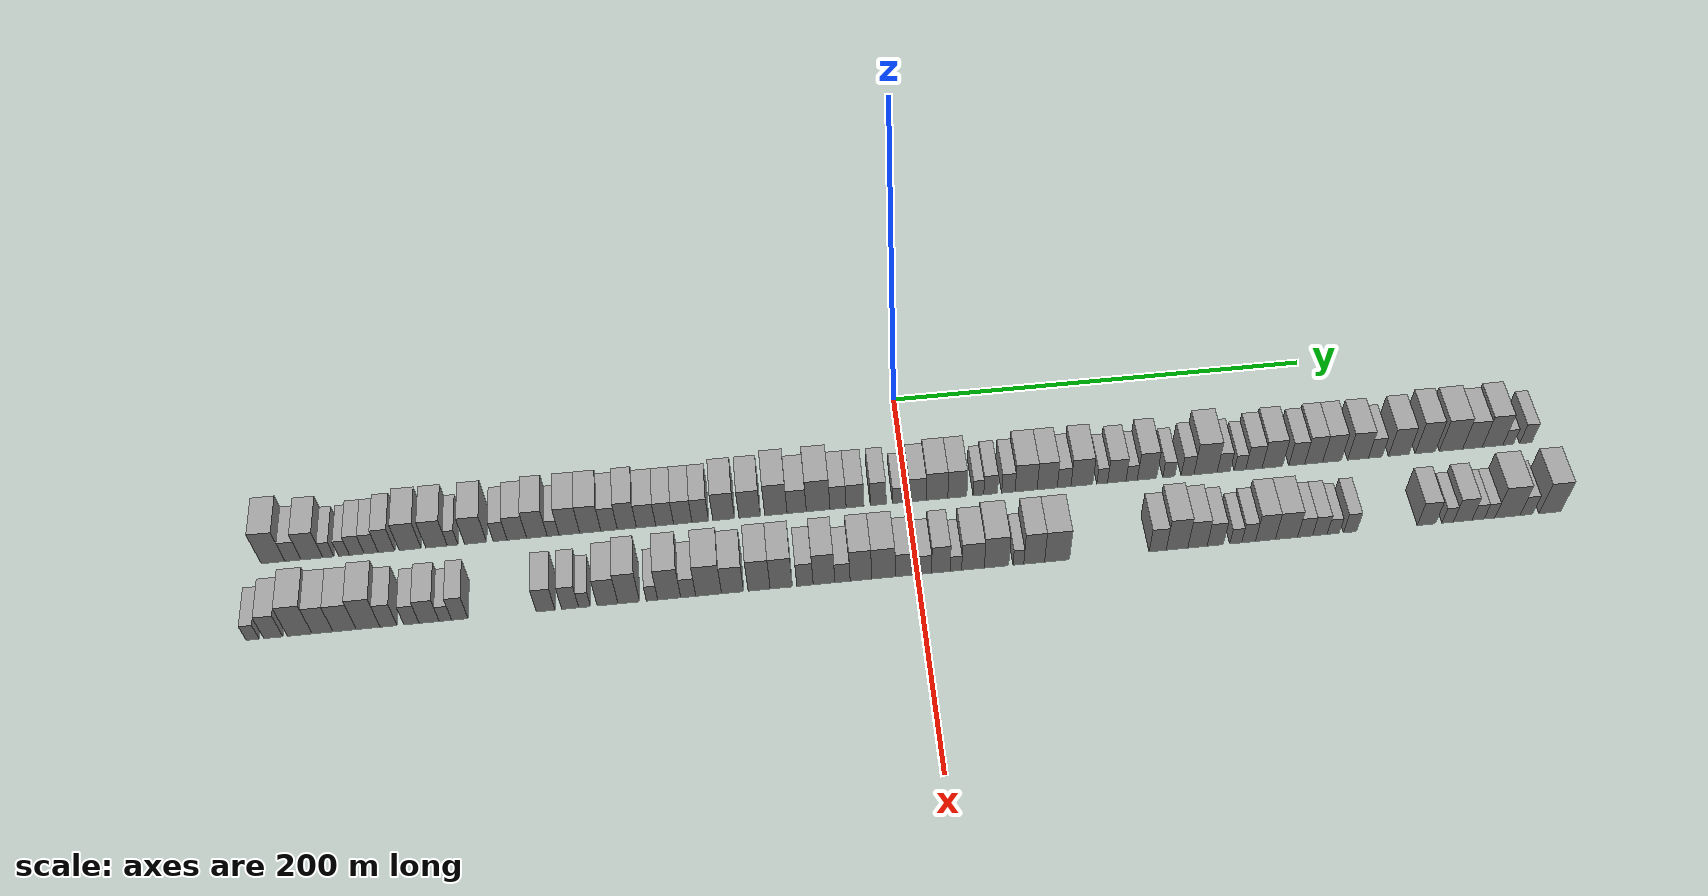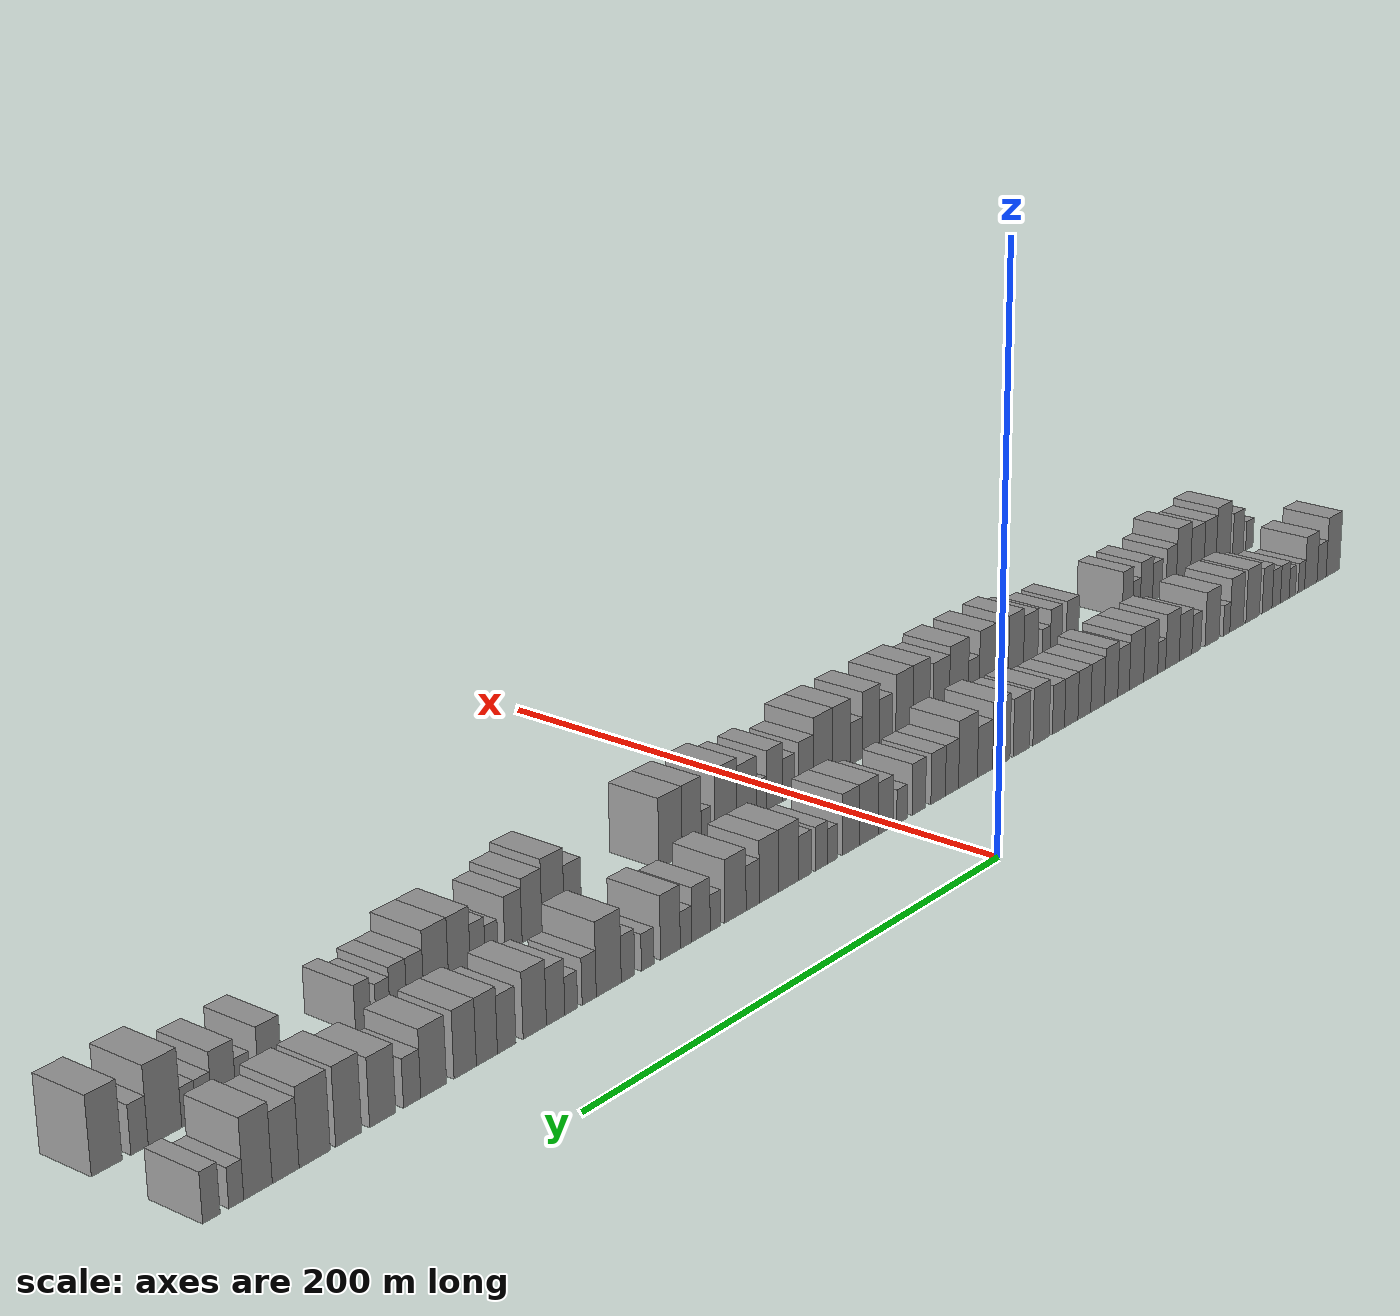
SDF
<sdf version="1.6">
 <world name="default">
  <scene>
   <sky><clouds><speed>12</speed></clouds></sky>
   <ambient>0.4 0.4 0.4 1</ambient>
   <background>0.7 0.7 0.7 1</background>
   <shadows>1</shadows>
  </scene>
  <gravity>0 0 -9.8066</gravity>
  <magnetic_field>6e-06 2.3e-05 -4.2e-05</magnetic_field>
  <physics default="0" name="default_physics" type="ode">
   <ode>
    <solver>
     <type>quick</type>
     <iters>10</iters>
     <sor>1.0</sor>
     <use_dynamic_moi_rescaling>0</use_dynamic_moi_rescaling>
    </solver>
    <constraints>
     <cfm>0</cfm>
     <erp>0.2</erp>
     <contact_max_correcting_vel>100</contact_max_correcting_vel>
     <contact_surface_layer>0.001</contact_surface_layer>
    </constraints>
   </ode>
   <max_step_size>0.004</max_step_size>
   <real_time_factor>1</real_time_factor>
   <real_time_update_rate>250</real_time_update_rate>
  </physics>
  <light name="sun" type="directional">
   <pose>0 0 10 0 0 0</pose>
   <diffuse>0.8 0.8 0.8 1</diffuse>
   <specular>0.2 0.2 0.2 1</specular>
   <attenuation>
    <range>1000</range>
    <constant>0.9</constant>
    <linear>0.01</linear>
    <quadratic>0.001</quadratic>
   </attenuation>
   <direction>-0.5 0.1 -0.9</direction>
  </light>
  <model name="building_1">
   <static>1</static>
   <pose>50.0000 -291.6410 0 0.000000 0.000000 0.000000</pose>
   <link name="link">
    <pose>0 0 12.00 0 0 0</pose>
    <collision name="collision"><geometry><box><size>20.0000 10.7179 24.0000</size></box></geometry></collision>
    <visual name="visual">
     <cast_shadows>0</cast_shadows>
     <geometry><box><size>20.0000 10.7179 24.0000</size></box></geometry>
     <material>
      <script>
       <uri>model://grey_wall/materials/scripts</uri>
       <uri>model://grey_wall/materials/textures</uri>
       <name>vrc/grey_wall</name>
      </script>
     </material>
    </visual>
   </link>
  </model>
  <model name="building_2">
   <static>1</static>
   <pose>50.0000 -282.6944 0 0.000000 0.000000 0.000000</pose>
   <link name="link">
    <pose>0 0 7.50 0 0 0</pose>
    <collision name="collision"><geometry><box><size>20.0000 7.1753 15.0000</size></box></geometry></collision>
    <visual name="visual">
     <cast_shadows>0</cast_shadows>
     <geometry><box><size>20.0000 7.1753 15.0000</size></box></geometry>
     <material>
      <script>
       <uri>model://grey_wall/materials/scripts</uri>
       <uri>model://grey_wall/materials/textures</uri>
       <name>vrc/grey_wall</name>
      </script>
     </material>
    </visual>
   </link>
  </model>
  <model name="building_3">
   <static>1</static>
   <pose>50.0000 -274.2108 0 0.000000 0.000000 0.000000</pose>
   <link name="link">
    <pose>0 0 10.50 0 0 0</pose>
    <collision name="collision"><geometry><box><size>20.0000 9.7919 21.0000</size></box></geometry></collision>
    <visual name="visual">
     <cast_shadows>0</cast_shadows>
     <geometry><box><size>20.0000 9.7919 21.0000</size></box></geometry>
     <material>
      <script>
       <uri>model://grey_wall/materials/scripts</uri>
       <uri>model://grey_wall/materials/textures</uri>
       <name>vrc/grey_wall</name>
      </script>
     </material>
    </visual>
   </link>
  </model>
  <model name="building_4">
   <static>1</static>
   <pose>50.0000 -266.7639 0 0.000000 0.000000 0.000000</pose>
   <link name="link">
    <pose>0 0 6.00 0 0 0</pose>
    <collision name="collision"><geometry><box><size>20.0000 5.1018 12.0000</size></box></geometry></collision>
    <visual name="visual">
     <cast_shadows>0</cast_shadows>
     <geometry><box><size>20.0000 5.1018 12.0000</size></box></geometry>
     <material>
      <script>
       <uri>model://grey_wall/materials/scripts</uri>
       <uri>model://grey_wall/materials/textures</uri>
       <name>vrc/grey_wall</name>
      </script>
     </material>
    </visual>
   </link>
  </model>
  <model name="building_5">
   <static>1</static>
   <pose>50.0000 -259.7612 0 0.000000 0.000000 0.000000</pose>
   <link name="link">
    <pose>0 0 6.00 0 0 0</pose>
    <collision name="collision"><geometry><box><size>20.0000 4.9035 12.0000</size></box></geometry></collision>
    <visual name="visual">
     <cast_shadows>0</cast_shadows>
     <geometry><box><size>20.0000 4.9035 12.0000</size></box></geometry>
     <material>
      <script>
       <uri>model://grey_wall/materials/scripts</uri>
       <uri>model://grey_wall/materials/textures</uri>
       <name>vrc/grey_wall</name>
      </script>
     </material>
    </visual>
   </link>
  </model>
  <model name="building_6">
   <static>1</static>
   <pose>50.0000 -253.9580 0 0.000000 0.000000 0.000000</pose>
   <link name="link">
    <pose>0 0 7.50 0 0 0</pose>
    <collision name="collision"><geometry><box><size>20.0000 6.7028 15.0000</size></box></geometry></collision>
    <visual name="visual">
     <cast_shadows>0</cast_shadows>
     <geometry><box><size>20.0000 6.7028 15.0000</size></box></geometry>
     <material>
      <script>
       <uri>model://grey_wall/materials/scripts</uri>
       <uri>model://grey_wall/materials/textures</uri>
       <name>vrc/grey_wall</name>
      </script>
     </material>
    </visual>
   </link>
  </model>
  <model name="building_7">
   <static>1</static>
   <pose>50.0000 -247.4439 0 0.000000 0.000000 0.000000</pose>
   <link name="link">
    <pose>0 0 7.50 0 0 0</pose>
    <collision name="collision"><geometry><box><size>20.0000 6.3254 15.0000</size></box></geometry></collision>
    <visual name="visual">
     <cast_shadows>0</cast_shadows>
     <geometry><box><size>20.0000 6.3254 15.0000</size></box></geometry>
     <material>
      <script>
       <uri>model://grey_wall/materials/scripts</uri>
       <uri>model://grey_wall/materials/textures</uri>
       <name>vrc/grey_wall</name>
      </script>
     </material>
    </visual>
   </link>
  </model>
  <model name="building_8">
   <static>1</static>
   <pose>50.0000 -240.5308 0 0.000000 0.000000 0.000000</pose>
   <link name="link">
    <pose>0 0 9.00 0 0 0</pose>
    <collision name="collision"><geometry><box><size>20.0000 7.5007 18.0000</size></box></geometry></collision>
    <visual name="visual">
     <cast_shadows>0</cast_shadows>
     <geometry><box><size>20.0000 7.5007 18.0000</size></box></geometry>
     <material>
      <script>
       <uri>model://grey_wall/materials/scripts</uri>
       <uri>model://grey_wall/materials/textures</uri>
       <name>vrc/grey_wall</name>
      </script>
     </material>
    </visual>
   </link>
  </model>
  <model name="building_9">
   <static>1</static>
   <pose>50.0000 -229.7729 0 0.000000 0.000000 0.000000</pose>
   <link name="link">
    <pose>0 0 10.50 0 0 0</pose>
    <collision name="collision"><geometry><box><size>20.0000 10.0150 21.0000</size></box></geometry></collision>
    <visual name="visual">
     <cast_shadows>0</cast_shadows>
     <geometry><box><size>20.0000 10.0150 21.0000</size></box></geometry>
     <material>
      <script>
       <uri>model://grey_wall/materials/scripts</uri>
       <uri>model://grey_wall/materials/textures</uri>
       <name>vrc/grey_wall</name>
      </script>
     </material>
    </visual>
   </link>
  </model>
  <model name="building_10">
   <static>1</static>
   <pose>50.0000 -217.8505 0 0.000000 0.000000 0.000000</pose>
   <link name="link">
    <pose>0 0 10.50 0 0 0</pose>
    <collision name="collision"><geometry><box><size>20.0000 9.8299 21.0000</size></box></geometry></collision>
    <visual name="visual">
     <cast_shadows>0</cast_shadows>
     <geometry><box><size>20.0000 9.8299 21.0000</size></box></geometry>
     <material>
      <script>
       <uri>model://grey_wall/materials/scripts</uri>
       <uri>model://grey_wall/materials/textures</uri>
       <name>vrc/grey_wall</name>
      </script>
     </material>
    </visual>
   </link>
  </model>
  <model name="building_11">
   <static>1</static>
   <pose>50.0000 -210.5100 0 0.000000 0.000000 0.000000</pose>
   <link name="link">
    <pose>0 0 6.00 0 0 0</pose>
    <collision name="collision"><geometry><box><size>20.0000 4.8512 12.0000</size></box></geometry></collision>
    <visual name="visual">
     <cast_shadows>0</cast_shadows>
     <geometry><box><size>20.0000 4.8512 12.0000</size></box></geometry>
     <material>
      <script>
       <uri>model://grey_wall/materials/scripts</uri>
       <uri>model://grey_wall/materials/textures</uri>
       <name>vrc/grey_wall</name>
      </script>
     </material>
    </visual>
   </link>
  </model>
  <model name="building_12">
   <static>1</static>
   <pose>50.0000 -200.0513 0 0.000000 0.000000 0.000000</pose>
   <link name="link">
    <pose>0 0 10.50 0 0 0</pose>
    <collision name="collision"><geometry><box><size>20.0000 10.0660 21.0000</size></box></geometry></collision>
    <visual name="visual">
     <cast_shadows>0</cast_shadows>
     <geometry><box><size>20.0000 10.0660 21.0000</size></box></geometry>
     <material>
      <script>
       <uri>model://grey_wall/materials/scripts</uri>
       <uri>model://grey_wall/materials/textures</uri>
       <name>vrc/grey_wall</name>
      </script>
     </material>
    </visual>
   </link>
  </model>
  <model name="building_13">
   <static>1</static>
   <pose>50.0000 -188.8611 0 0.000000 0.000000 0.000000</pose>
   <link name="link">
    <pose>0 0 7.50 0 0 0</pose>
    <collision name="collision"><geometry><box><size>20.0000 6.3144 15.0000</size></box></geometry></collision>
    <visual name="visual">
     <cast_shadows>0</cast_shadows>
     <geometry><box><size>20.0000 6.3144 15.0000</size></box></geometry>
     <material>
      <script>
       <uri>model://grey_wall/materials/scripts</uri>
       <uri>model://grey_wall/materials/textures</uri>
       <name>vrc/grey_wall</name>
      </script>
     </material>
    </visual>
   </link>
  </model>
  <model name="building_14">
   <static>1</static>
   <pose>50.0000 -181.2198 0 0.000000 0.000000 0.000000</pose>
   <link name="link">
    <pose>0 0 9.00 0 0 0</pose>
    <collision name="collision"><geometry><box><size>20.0000 8.9682 18.0000</size></box></geometry></collision>
    <visual name="visual">
     <cast_shadows>0</cast_shadows>
     <geometry><box><size>20.0000 8.9682 18.0000</size></box></geometry>
     <material>
      <script>
       <uri>model://grey_wall/materials/scripts</uri>
       <uri>model://grey_wall/materials/textures</uri>
       <name>vrc/grey_wall</name>
      </script>
     </material>
    </visual>
   </link>
  </model>
  <model name="building_15">
   <static>1</static>
   <pose>50.0000 -172.0450 0 0.000000 0.000000 0.000000</pose>
   <link name="link">
    <pose>0 0 10.50 0 0 0</pose>
    <collision name="collision"><geometry><box><size>20.0000 9.3814 21.0000</size></box></geometry></collision>
    <visual name="visual">
     <cast_shadows>0</cast_shadows>
     <geometry><box><size>20.0000 9.3814 21.0000</size></box></geometry>
     <material>
      <script>
       <uri>model://grey_wall/materials/scripts</uri>
       <uri>model://grey_wall/materials/textures</uri>
       <name>vrc/grey_wall</name>
      </script>
     </material>
    </visual>
   </link>
  </model>
  <model name="building_16">
   <static>1</static>
   <pose>50.0000 -164.6468 0 0.000000 0.000000 0.000000</pose>
   <link name="link">
    <pose>0 0 6.00 0 0 0</pose>
    <collision name="collision"><geometry><box><size>20.0000 5.4151 12.0000</size></box></geometry></collision>
    <visual name="visual">
     <cast_shadows>0</cast_shadows>
     <geometry><box><size>20.0000 5.4151 12.0000</size></box></geometry>
     <material>
      <script>
       <uri>model://grey_wall/materials/scripts</uri>
       <uri>model://grey_wall/materials/textures</uri>
       <name>vrc/grey_wall</name>
      </script>
     </material>
    </visual>
   </link>
  </model>
  <model name="building_17">
   <static>1</static>
   <pose>50.0000 -157.1940 0 0.000000 0.000000 0.000000</pose>
   <link name="link">
    <pose>0 0 10.50 0 0 0</pose>
    <collision name="collision"><geometry><box><size>20.0000 9.4905 21.0000</size></box></geometry></collision>
    <visual name="visual">
     <cast_shadows>0</cast_shadows>
     <geometry><box><size>20.0000 9.4905 21.0000</size></box></geometry>
     <material>
      <script>
       <uri>model://grey_wall/materials/scripts</uri>
       <uri>model://grey_wall/materials/textures</uri>
       <name>vrc/grey_wall</name>
      </script>
     </material>
    </visual>
   </link>
  </model>
  <model name="building_18">
   <static>1</static>
   <pose>50.0000 -147.5965 0 0.000000 0.000000 0.000000</pose>
   <link name="link">
    <pose>0 0 10.50 0 0 0</pose>
    <collision name="collision"><geometry><box><size>20.0000 9.7044 21.0000</size></box></geometry></collision>
    <visual name="visual">
     <cast_shadows>0</cast_shadows>
     <geometry><box><size>20.0000 9.7044 21.0000</size></box></geometry>
     <material>
      <script>
       <uri>model://grey_wall/materials/scripts</uri>
       <uri>model://grey_wall/materials/textures</uri>
       <name>vrc/grey_wall</name>
      </script>
     </material>
    </visual>
   </link>
  </model>
  <model name="building_19">
   <static>1</static>
   <pose>50.0000 -138.9264 0 0.000000 0.000000 0.000000</pose>
   <link name="link">
    <pose>0 0 9.00 0 0 0</pose>
    <collision name="collision"><geometry><box><size>20.0000 7.6358 18.0000</size></box></geometry></collision>
    <visual name="visual">
     <cast_shadows>0</cast_shadows>
     <geometry><box><size>20.0000 7.6358 18.0000</size></box></geometry>
     <material>
      <script>
       <uri>model://grey_wall/materials/scripts</uri>
       <uri>model://grey_wall/materials/textures</uri>
       <name>vrc/grey_wall</name>
      </script>
     </material>
    </visual>
   </link>
  </model>
  <model name="building_20">
   <static>1</static>
   <pose>50.0000 -130.7200 0 0.000000 0.000000 0.000000</pose>
   <link name="link">
    <pose>0 0 10.50 0 0 0</pose>
    <collision name="collision"><geometry><box><size>20.0000 8.7770 21.0000</size></box></geometry></collision>
    <visual name="visual">
     <cast_shadows>0</cast_shadows>
     <geometry><box><size>20.0000 8.7770 21.0000</size></box></geometry>
     <material>
      <script>
       <uri>model://grey_wall/materials/scripts</uri>
       <uri>model://grey_wall/materials/textures</uri>
       <name>vrc/grey_wall</name>
      </script>
     </material>
    </visual>
   </link>
  </model>
  <model name="building_21">
   <static>1</static>
   <pose>50.0000 -121.8739 0 0.000000 0.000000 0.000000</pose>
   <link name="link">
    <pose>0 0 9.00 0 0 0</pose>
    <collision name="collision"><geometry><box><size>20.0000 8.9151 18.0000</size></box></geometry></collision>
    <visual name="visual">
     <cast_shadows>0</cast_shadows>
     <geometry><box><size>20.0000 8.9151 18.0000</size></box></geometry>
     <material>
      <script>
       <uri>model://grey_wall/materials/scripts</uri>
       <uri>model://grey_wall/materials/textures</uri>
       <name>vrc/grey_wall</name>
      </script>
     </material>
    </visual>
   </link>
  </model>
  <model name="building_22">
   <static>1</static>
   <pose>50.0000 -113.3084 0 0.000000 0.000000 0.000000</pose>
   <link name="link">
    <pose>0 0 9.00 0 0 0</pose>
    <collision name="collision"><geometry><box><size>20.0000 8.2160 18.0000</size></box></geometry></collision>
    <visual name="visual">
     <cast_shadows>0</cast_shadows>
     <geometry><box><size>20.0000 8.2160 18.0000</size></box></geometry>
     <material>
      <script>
       <uri>model://grey_wall/materials/scripts</uri>
       <uri>model://grey_wall/materials/textures</uri>
       <name>vrc/grey_wall</name>
      </script>
     </material>
    </visual>
   </link>
  </model>
  <model name="building_23">
   <static>1</static>
   <pose>50.0000 -104.9316 0 0.000000 0.000000 0.000000</pose>
   <link name="link">
    <pose>0 0 9.00 0 0 0</pose>
    <collision name="collision"><geometry><box><size>20.0000 8.5375 18.0000</size></box></geometry></collision>
    <visual name="visual">
     <cast_shadows>0</cast_shadows>
     <geometry><box><size>20.0000 8.5375 18.0000</size></box></geometry>
     <material>
      <script>
       <uri>model://grey_wall/materials/scripts</uri>
       <uri>model://grey_wall/materials/textures</uri>
       <name>vrc/grey_wall</name>
      </script>
     </material>
    </visual>
   </link>
  </model>
  <model name="building_24">
   <static>1</static>
   <pose>50.0000 -96.8348 0 0.000000 0.000000 0.000000</pose>
   <link name="link">
    <pose>0 0 9.00 0 0 0</pose>
    <collision name="collision"><geometry><box><size>20.0000 7.6561 18.0000</size></box></geometry></collision>
    <visual name="visual">
     <cast_shadows>0</cast_shadows>
     <geometry><box><size>20.0000 7.6561 18.0000</size></box></geometry>
     <material>
      <script>
       <uri>model://grey_wall/materials/scripts</uri>
       <uri>model://grey_wall/materials/textures</uri>
       <name>vrc/grey_wall</name>
      </script>
     </material>
    </visual>
   </link>
  </model>
  <model name="building_25">
   <static>1</static>
   <pose>50.0000 -85.9560 0 0.000000 0.000000 0.000000</pose>
   <link name="link">
    <pose>0 0 10.50 0 0 0</pose>
    <collision name="collision"><geometry><box><size>20.0000 10.1015 21.0000</size></box></geometry></collision>
    <visual name="visual">
     <cast_shadows>0</cast_shadows>
     <geometry><box><size>20.0000 10.1015 21.0000</size></box></geometry>
     <material>
      <script>
       <uri>model://grey_wall/materials/scripts</uri>
       <uri>model://grey_wall/materials/textures</uri>
       <name>vrc/grey_wall</name>
      </script>
     </material>
    </visual>
   </link>
  </model>
  <model name="building_26">
   <static>1</static>
   <pose>50.0000 -73.9117 0 0.000000 0.000000 0.000000</pose>
   <link name="link">
    <pose>0 0 10.50 0 0 0</pose>
    <collision name="collision"><geometry><box><size>20.0000 9.9872 21.0000</size></box></geometry></collision>
    <visual name="visual">
     <cast_shadows>0</cast_shadows>
     <geometry><box><size>20.0000 9.9872 21.0000</size></box></geometry>
     <material>
      <script>
       <uri>model://grey_wall/materials/scripts</uri>
       <uri>model://grey_wall/materials/textures</uri>
       <name>vrc/grey_wall</name>
      </script>
     </material>
    </visual>
   </link>
  </model>
  <model name="building_27">
   <static>1</static>
   <pose>50.0000 -61.7205 0 0.000000 0.000000 0.000000</pose>
   <link name="link">
    <pose>0 0 12.00 0 0 0</pose>
    <collision name="collision"><geometry><box><size>20.0000 10.3952 24.0000</size></box></geometry></collision>
    <visual name="visual">
     <cast_shadows>0</cast_shadows>
     <geometry><box><size>20.0000 10.3952 24.0000</size></box></geometry>
     <material>
      <script>
       <uri>model://grey_wall/materials/scripts</uri>
       <uri>model://grey_wall/materials/textures</uri>
       <name>vrc/grey_wall</name>
      </script>
     </material>
    </visual>
   </link>
  </model>
  <model name="building_28">
   <static>1</static>
   <pose>50.0000 -52.0402 0 0.000000 0.000000 0.000000</pose>
   <link name="link">
    <pose>0 0 9.00 0 0 0</pose>
    <collision name="collision"><geometry><box><size>20.0000 8.9653 18.0000</size></box></geometry></collision>
    <visual name="visual">
     <cast_shadows>0</cast_shadows>
     <geometry><box><size>20.0000 8.9653 18.0000</size></box></geometry>
     <material>
      <script>
       <uri>model://grey_wall/materials/scripts</uri>
       <uri>model://grey_wall/materials/textures</uri>
       <name>vrc/grey_wall</name>
      </script>
     </material>
    </visual>
   </link>
  </model>
  <model name="building_29">
   <static>1</static>
   <pose>50.0000 -42.0420 0 0.000000 0.000000 0.000000</pose>
   <link name="link">
    <pose>0 0 12.00 0 0 0</pose>
    <collision name="collision"><geometry><box><size>20.0000 11.0312 24.0000</size></box></geometry></collision>
    <visual name="visual">
     <cast_shadows>0</cast_shadows>
     <geometry><box><size>20.0000 11.0312 24.0000</size></box></geometry>
     <material>
      <script>
       <uri>model://grey_wall/materials/scripts</uri>
       <uri>model://grey_wall/materials/textures</uri>
       <name>vrc/grey_wall</name>
      </script>
     </material>
    </visual>
   </link>
  </model>
  <model name="building_30">
   <static>1</static>
   <pose>50.0000 -32.7494 0 0.000000 0.000000 0.000000</pose>
   <link name="link">
    <pose>0 0 9.00 0 0 0</pose>
    <collision name="collision"><geometry><box><size>20.0000 7.5539 18.0000</size></box></geometry></collision>
    <visual name="visual">
     <cast_shadows>0</cast_shadows>
     <geometry><box><size>20.0000 7.5539 18.0000</size></box></geometry>
     <material>
      <script>
       <uri>model://grey_wall/materials/scripts</uri>
       <uri>model://grey_wall/materials/textures</uri>
       <name>vrc/grey_wall</name>
      </script>
     </material>
    </visual>
   </link>
  </model>
  <model name="building_31">
   <static>1</static>
   <pose>50.0000 -24.8039 0 0.000000 0.000000 0.000000</pose>
   <link name="link">
    <pose>0 0 9.00 0 0 0</pose>
    <collision name="collision"><geometry><box><size>20.0000 8.3371 18.0000</size></box></geometry></collision>
    <visual name="visual">
     <cast_shadows>0</cast_shadows>
     <geometry><box><size>20.0000 8.3371 18.0000</size></box></geometry>
     <material>
      <script>
       <uri>model://grey_wall/materials/scripts</uri>
       <uri>model://grey_wall/materials/textures</uri>
       <name>vrc/grey_wall</name>
      </script>
     </material>
    </visual>
   </link>
  </model>
  <model name="building_32">
   <static>1</static>
   <pose>50.0000 -13.9315 0 0.000000 0.000000 0.000000</pose>
   <link name="link">
    <pose>0 0 9.00 0 0 0</pose>
    <collision name="collision"><geometry><box><size>20.0000 7.4077 18.0000</size></box></geometry></collision>
    <visual name="visual">
     <cast_shadows>0</cast_shadows>
     <geometry><box><size>20.0000 7.4077 18.0000</size></box></geometry>
     <material>
      <script>
       <uri>model://grey_wall/materials/scripts</uri>
       <uri>model://grey_wall/materials/textures</uri>
       <name>vrc/grey_wall</name>
      </script>
     </material>
    </visual>
   </link>
  </model>
  <model name="building_33">
   <static>1</static>
   <pose>50.0000 -4.3813 0 0.000000 0.000000 0.000000</pose>
   <link name="link">
    <pose>0 0 6.00 0 0 0</pose>
    <collision name="collision"><geometry><box><size>20.0000 5.6928 12.0000</size></box></geometry></collision>
    <visual name="visual">
     <cast_shadows>0</cast_shadows>
     <geometry><box><size>20.0000 5.6928 12.0000</size></box></geometry>
     <material>
      <script>
       <uri>model://grey_wall/materials/scripts</uri>
       <uri>model://grey_wall/materials/textures</uri>
       <name>vrc/grey_wall</name>
      </script>
     </material>
    </visual>
   </link>
  </model>
  <model name="building_34">
   <static>1</static>
   <pose>50.0000 4.6034 0 0.000000 0.000000 0.000000</pose>
   <link name="link">
    <pose>0 0 9.00 0 0 0</pose>
    <collision name="collision"><geometry><box><size>20.0000 8.2765 18.0000</size></box></geometry></collision>
    <visual name="visual">
     <cast_shadows>0</cast_shadows>
     <geometry><box><size>20.0000 8.2765 18.0000</size></box></geometry>
     <material>
      <script>
       <uri>model://grey_wall/materials/scripts</uri>
       <uri>model://grey_wall/materials/textures</uri>
       <name>vrc/grey_wall</name>
      </script>
     </material>
    </visual>
   </link>
  </model>
  <model name="building_35">
   <static>1</static>
   <pose>50.0000 13.7595 0 0.000000 0.000000 0.000000</pose>
   <link name="link">
    <pose>0 0 10.50 0 0 0</pose>
    <collision name="collision"><geometry><box><size>20.0000 10.0357 21.0000</size></box></geometry></collision>
    <visual name="visual">
     <cast_shadows>0</cast_shadows>
     <geometry><box><size>20.0000 10.0357 21.0000</size></box></geometry>
     <material>
      <script>
       <uri>model://grey_wall/materials/scripts</uri>
       <uri>model://grey_wall/materials/textures</uri>
       <name>vrc/grey_wall</name>
      </script>
     </material>
    </visual>
   </link>
  </model>
  <model name="building_36">
   <static>1</static>
   <pose>50.0000 23.2460 0 0.000000 0.000000 0.000000</pose>
   <link name="link">
    <pose>0 0 10.50 0 0 0</pose>
    <collision name="collision"><geometry><box><size>20.0000 8.9372 21.0000</size></box></geometry></collision>
    <visual name="visual">
     <cast_shadows>0</cast_shadows>
     <geometry><box><size>20.0000 8.9372 21.0000</size></box></geometry>
     <material>
      <script>
       <uri>model://grey_wall/materials/scripts</uri>
       <uri>model://grey_wall/materials/textures</uri>
       <name>vrc/grey_wall</name>
      </script>
     </material>
    </visual>
   </link>
  </model>
  <model name="building_37">
   <static>1</static>
   <pose>50.0000 33.2206 0 0.000000 0.000000 0.000000</pose>
   <link name="link">
    <pose>0 0 6.00 0 0 0</pose>
    <collision name="collision"><geometry><box><size>20.0000 5.0121 12.0000</size></box></geometry></collision>
    <visual name="visual">
     <cast_shadows>0</cast_shadows>
     <geometry><box><size>20.0000 5.0121 12.0000</size></box></geometry>
     <material>
      <script>
       <uri>model://grey_wall/materials/scripts</uri>
       <uri>model://grey_wall/materials/textures</uri>
       <name>vrc/grey_wall</name>
      </script>
     </material>
    </visual>
   </link>
  </model>
  <model name="building_38">
   <static>1</static>
   <pose>50.0000 38.9742 0 0.000000 0.000000 0.000000</pose>
   <link name="link">
    <pose>0 0 7.50 0 0 0</pose>
    <collision name="collision"><geometry><box><size>20.0000 6.4951 15.0000</size></box></geometry></collision>
    <visual name="visual">
     <cast_shadows>0</cast_shadows>
     <geometry><box><size>20.0000 6.4951 15.0000</size></box></geometry>
     <material>
      <script>
       <uri>model://grey_wall/materials/scripts</uri>
       <uri>model://grey_wall/materials/textures</uri>
       <name>vrc/grey_wall</name>
      </script>
     </material>
    </visual>
   </link>
  </model>
  <model name="building_39">
   <static>1</static>
   <pose>50.0000 47.3750 0 0.000000 0.000000 0.000000</pose>
   <link name="link">
    <pose>0 0 7.50 0 0 0</pose>
    <collision name="collision"><geometry><box><size>20.0000 6.3065 15.0000</size></box></geometry></collision>
    <visual name="visual">
     <cast_shadows>0</cast_shadows>
     <geometry><box><size>20.0000 6.3065 15.0000</size></box></geometry>
     <material>
      <script>
       <uri>model://grey_wall/materials/scripts</uri>
       <uri>model://grey_wall/materials/textures</uri>
       <name>vrc/grey_wall</name>
      </script>
     </material>
    </visual>
   </link>
  </model>
  <model name="building_40">
   <static>1</static>
   <pose>50.0000 55.7754 0 0.000000 0.000000 0.000000</pose>
   <link name="link">
    <pose>0 0 10.50 0 0 0</pose>
    <collision name="collision"><geometry><box><size>20.0000 10.4942 21.0000</size></box></geometry></collision>
    <visual name="visual">
     <cast_shadows>0</cast_shadows>
     <geometry><box><size>20.0000 10.4942 21.0000</size></box></geometry>
     <material>
      <script>
       <uri>model://grey_wall/materials/scripts</uri>
       <uri>model://grey_wall/materials/textures</uri>
       <name>vrc/grey_wall</name>
      </script>
     </material>
    </visual>
   </link>
  </model>
  <model name="building_41">
   <static>1</static>
   <pose>50.0000 65.7704 0 0.000000 0.000000 0.000000</pose>
   <link name="link">
    <pose>0 0 10.50 0 0 0</pose>
    <collision name="collision"><geometry><box><size>20.0000 9.4959 21.0000</size></box></geometry></collision>
    <visual name="visual">
     <cast_shadows>0</cast_shadows>
     <geometry><box><size>20.0000 9.4959 21.0000</size></box></geometry>
     <material>
      <script>
       <uri>model://grey_wall/materials/scripts</uri>
       <uri>model://grey_wall/materials/textures</uri>
       <name>vrc/grey_wall</name>
      </script>
     </material>
    </visual>
   </link>
  </model>
  <model name="building_42">
   <static>1</static>
   <pose>50.0000 73.7756 0 0.000000 0.000000 0.000000</pose>
   <link name="link">
    <pose>0 0 7.50 0 0 0</pose>
    <collision name="collision"><geometry><box><size>20.0000 6.5145 15.0000</size></box></geometry></collision>
    <visual name="visual">
     <cast_shadows>0</cast_shadows>
     <geometry><box><size>20.0000 6.5145 15.0000</size></box></geometry>
     <material>
      <script>
       <uri>model://grey_wall/materials/scripts</uri>
       <uri>model://grey_wall/materials/textures</uri>
       <name>vrc/grey_wall</name>
      </script>
     </material>
    </visual>
   </link>
  </model>
  <model name="building_43">
   <static>1</static>
   <pose>50.0000 82.2063 0 0.000000 0.000000 0.000000</pose>
   <link name="link">
    <pose>0 0 10.50 0 0 0</pose>
    <collision name="collision"><geometry><box><size>20.0000 10.3469 21.0000</size></box></geometry></collision>
    <visual name="visual">
     <cast_shadows>0</cast_shadows>
     <geometry><box><size>20.0000 10.3469 21.0000</size></box></geometry>
     <material>
      <script>
       <uri>model://grey_wall/materials/scripts</uri>
       <uri>model://grey_wall/materials/textures</uri>
       <name>vrc/grey_wall</name>
      </script>
     </material>
    </visual>
   </link>
  </model>
  <model name="building_44">
   <static>1</static>
   <pose>50.0000 91.9267 0 0.000000 0.000000 0.000000</pose>
   <link name="link">
    <pose>0 0 6.00 0 0 0</pose>
    <collision name="collision"><geometry><box><size>20.0000 5.0939 12.0000</size></box></geometry></collision>
    <visual name="visual">
     <cast_shadows>0</cast_shadows>
     <geometry><box><size>20.0000 5.0939 12.0000</size></box></geometry>
     <material>
      <script>
       <uri>model://grey_wall/materials/scripts</uri>
       <uri>model://grey_wall/materials/textures</uri>
       <name>vrc/grey_wall</name>
      </script>
     </material>
    </visual>
   </link>
  </model>
  <model name="building_45">
   <static>1</static>
   <pose>50.0000 98.8764 0 0.000000 0.000000 0.000000</pose>
   <link name="link">
    <pose>0 0 9.00 0 0 0</pose>
    <collision name="collision"><geometry><box><size>20.0000 8.8055 18.0000</size></box></geometry></collision>
    <visual name="visual">
     <cast_shadows>0</cast_shadows>
     <geometry><box><size>20.0000 8.8055 18.0000</size></box></geometry>
     <material>
      <script>
       <uri>model://grey_wall/materials/scripts</uri>
       <uri>model://grey_wall/materials/textures</uri>
       <name>vrc/grey_wall</name>
      </script>
     </material>
    </visual>
   </link>
  </model>
  <model name="building_46">
   <static>1</static>
   <pose>50.0000 105.9861 0 0.000000 0.000000 0.000000</pose>
   <link name="link">
    <pose>0 0 6.00 0 0 0</pose>
    <collision name="collision"><geometry><box><size>20.0000 5.4139 12.0000</size></box></geometry></collision>
    <visual name="visual">
     <cast_shadows>0</cast_shadows>
     <geometry><box><size>20.0000 5.4139 12.0000</size></box></geometry>
     <material>
      <script>
       <uri>model://grey_wall/materials/scripts</uri>
       <uri>model://grey_wall/materials/textures</uri>
       <name>vrc/grey_wall</name>
      </script>
     </material>
    </visual>
   </link>
  </model>
  <model name="building_47">
   <static>1</static>
   <pose>50.0000 113.2934 0 0.000000 0.000000 0.000000</pose>
   <link name="link">
    <pose>0 0 10.50 0 0 0</pose>
    <collision name="collision"><geometry><box><size>20.0000 9.2007 21.0000</size></box></geometry></collision>
    <visual name="visual">
     <cast_shadows>0</cast_shadows>
     <geometry><box><size>20.0000 9.2007 21.0000</size></box></geometry>
     <material>
      <script>
       <uri>model://grey_wall/materials/scripts</uri>
       <uri>model://grey_wall/materials/textures</uri>
       <name>vrc/grey_wall</name>
      </script>
     </material>
    </visual>
   </link>
  </model>
  <model name="building_48">
   <static>1</static>
   <pose>50.0000 123.7985 0 0.000000 0.000000 0.000000</pose>
   <link name="link">
    <pose>0 0 6.00 0 0 0</pose>
    <collision name="collision"><geometry><box><size>20.0000 5.8095 12.0000</size></box></geometry></collision>
    <visual name="visual">
     <cast_shadows>0</cast_shadows>
     <geometry><box><size>20.0000 5.8095 12.0000</size></box></geometry>
     <material>
      <script>
       <uri>model://grey_wall/materials/scripts</uri>
       <uri>model://grey_wall/materials/textures</uri>
       <name>vrc/grey_wall</name>
      </script>
     </material>
    </visual>
   </link>
  </model>
  <model name="building_49">
   <static>1</static>
   <pose>50.0000 132.7728 0 0.000000 0.000000 0.000000</pose>
   <link name="link">
    <pose>0 0 7.50 0 0 0</pose>
    <collision name="collision"><geometry><box><size>20.0000 6.1389 15.0000</size></box></geometry></collision>
    <visual name="visual">
     <cast_shadows>0</cast_shadows>
     <geometry><box><size>20.0000 6.1389 15.0000</size></box></geometry>
     <material>
      <script>
       <uri>model://grey_wall/materials/scripts</uri>
       <uri>model://grey_wall/materials/textures</uri>
       <name>vrc/grey_wall</name>
      </script>
     </material>
    </visual>
   </link>
  </model>
  <model name="building_50">
   <static>1</static>
   <pose>50.0000 141.4170 0 0.000000 0.000000 0.000000</pose>
   <link name="link">
    <pose>0 0 12.00 0 0 0</pose>
    <collision name="collision"><geometry><box><size>20.0000 11.1495 24.0000</size></box></geometry></collision>
    <visual name="visual">
     <cast_shadows>0</cast_shadows>
     <geometry><box><size>20.0000 11.1495 24.0000</size></box></geometry>
     <material>
      <script>
       <uri>model://grey_wall/materials/scripts</uri>
       <uri>model://grey_wall/materials/textures</uri>
       <name>vrc/grey_wall</name>
      </script>
     </material>
    </visual>
   </link>
  </model>
  <model name="building_51">
   <static>1</static>
   <pose>50.0000 150.1050 0 0.000000 0.000000 0.000000</pose>
   <link name="link">
    <pose>0 0 7.50 0 0 0</pose>
    <collision name="collision"><geometry><box><size>20.0000 6.2265 15.0000</size></box></geometry></collision>
    <visual name="visual">
     <cast_shadows>0</cast_shadows>
     <geometry><box><size>20.0000 6.2265 15.0000</size></box></geometry>
     <material>
      <script>
       <uri>model://grey_wall/materials/scripts</uri>
       <uri>model://grey_wall/materials/textures</uri>
       <name>vrc/grey_wall</name>
      </script>
     </material>
    </visual>
   </link>
  </model>
  <model name="building_52">
   <static>1</static>
   <pose>50.0000 157.9779 0 0.000000 0.000000 0.000000</pose>
   <link name="link">
    <pose>0 0 6.00 0 0 0</pose>
    <collision name="collision"><geometry><box><size>20.0000 5.5194 12.0000</size></box></geometry></collision>
    <visual name="visual">
     <cast_shadows>0</cast_shadows>
     <geometry><box><size>20.0000 5.5194 12.0000</size></box></geometry>
     <material>
      <script>
       <uri>model://grey_wall/materials/scripts</uri>
       <uri>model://grey_wall/materials/textures</uri>
       <name>vrc/grey_wall</name>
      </script>
     </material>
    </visual>
   </link>
  </model>
  <model name="building_53">
   <static>1</static>
   <pose>50.0000 164.7002 0 0.000000 0.000000 0.000000</pose>
   <link name="link">
    <pose>0 0 9.00 0 0 0</pose>
    <collision name="collision"><geometry><box><size>20.0000 7.9251 18.0000</size></box></geometry></collision>
    <visual name="visual">
     <cast_shadows>0</cast_shadows>
     <geometry><box><size>20.0000 7.9251 18.0000</size></box></geometry>
     <material>
      <script>
       <uri>model://grey_wall/materials/scripts</uri>
       <uri>model://grey_wall/materials/textures</uri>
       <name>vrc/grey_wall</name>
      </script>
     </material>
    </visual>
   </link>
  </model>
  <model name="building_54">
   <static>1</static>
   <pose>50.0000 173.6147 0 0.000000 0.000000 0.000000</pose>
   <link name="link">
    <pose>0 0 10.50 0 0 0</pose>
    <collision name="collision"><geometry><box><size>20.0000 9.9040 21.0000</size></box></geometry></collision>
    <visual name="visual">
     <cast_shadows>0</cast_shadows>
     <geometry><box><size>20.0000 9.9040 21.0000</size></box></geometry>
     <material>
      <script>
       <uri>model://grey_wall/materials/scripts</uri>
       <uri>model://grey_wall/materials/textures</uri>
       <name>vrc/grey_wall</name>
      </script>
     </material>
    </visual>
   </link>
  </model>
  <model name="building_55">
   <static>1</static>
   <pose>50.0000 185.4080 0 0.000000 0.000000 0.000000</pose>
   <link name="link">
    <pose>0 0 9.00 0 0 0</pose>
    <collision name="collision"><geometry><box><size>20.0000 7.6825 18.0000</size></box></geometry></collision>
    <visual name="visual">
     <cast_shadows>0</cast_shadows>
     <geometry><box><size>20.0000 7.6825 18.0000</size></box></geometry>
     <material>
      <script>
       <uri>model://grey_wall/materials/scripts</uri>
       <uri>model://grey_wall/materials/textures</uri>
       <name>vrc/grey_wall</name>
      </script>
     </material>
    </visual>
   </link>
  </model>
  <model name="building_56">
   <static>1</static>
   <pose>50.0000 193.5839 0 0.000000 0.000000 0.000000</pose>
   <link name="link">
    <pose>0 0 10.50 0 0 0</pose>
    <collision name="collision"><geometry><box><size>20.0000 8.6694 21.0000</size></box></geometry></collision>
    <visual name="visual">
     <cast_shadows>0</cast_shadows>
     <geometry><box><size>20.0000 8.6694 21.0000</size></box></geometry>
     <material>
      <script>
       <uri>model://grey_wall/materials/scripts</uri>
       <uri>model://grey_wall/materials/textures</uri>
       <name>vrc/grey_wall</name>
      </script>
     </material>
    </visual>
   </link>
  </model>
  <model name="building_57">
   <static>1</static>
   <pose>50.0000 202.4442 0 0.000000 0.000000 0.000000</pose>
   <link name="link">
    <pose>0 0 10.50 0 0 0</pose>
    <collision name="collision"><geometry><box><size>20.0000 9.0514 21.0000</size></box></geometry></collision>
    <visual name="visual">
     <cast_shadows>0</cast_shadows>
     <geometry><box><size>20.0000 9.0514 21.0000</size></box></geometry>
     <material>
      <script>
       <uri>model://grey_wall/materials/scripts</uri>
       <uri>model://grey_wall/materials/textures</uri>
       <name>vrc/grey_wall</name>
      </script>
     </material>
    </visual>
   </link>
  </model>
  <model name="building_58">
   <static>1</static>
   <pose>50.0000 215.0470 0 0.000000 0.000000 0.000000</pose>
   <link name="link">
    <pose>0 0 10.50 0 0 0</pose>
    <collision name="collision"><geometry><box><size>20.0000 10.1541 21.0000</size></box></geometry></collision>
    <visual name="visual">
     <cast_shadows>0</cast_shadows>
     <geometry><box><size>20.0000 10.1541 21.0000</size></box></geometry>
     <material>
      <script>
       <uri>model://grey_wall/materials/scripts</uri>
       <uri>model://grey_wall/materials/textures</uri>
       <name>vrc/grey_wall</name>
      </script>
     </material>
    </visual>
   </link>
  </model>
  <model name="building_59">
   <static>1</static>
   <pose>50.0000 223.5183 0 0.000000 0.000000 0.000000</pose>
   <link name="link">
    <pose>0 0 7.50 0 0 0</pose>
    <collision name="collision"><geometry><box><size>20.0000 6.7885 15.0000</size></box></geometry></collision>
    <visual name="visual">
     <cast_shadows>0</cast_shadows>
     <geometry><box><size>20.0000 6.7885 15.0000</size></box></geometry>
     <material>
      <script>
       <uri>model://grey_wall/materials/scripts</uri>
       <uri>model://grey_wall/materials/textures</uri>
       <name>vrc/grey_wall</name>
      </script>
     </material>
    </visual>
   </link>
  </model>
  <model name="building_60">
   <static>1</static>
   <pose>50.0000 234.9215 0 0.000000 0.000000 0.000000</pose>
   <link name="link">
    <pose>0 0 10.50 0 0 0</pose>
    <collision name="collision"><geometry><box><size>20.0000 10.0179 21.0000</size></box></geometry></collision>
    <visual name="visual">
     <cast_shadows>0</cast_shadows>
     <geometry><box><size>20.0000 10.0179 21.0000</size></box></geometry>
     <material>
      <script>
       <uri>model://grey_wall/materials/scripts</uri>
       <uri>model://grey_wall/materials/textures</uri>
       <name>vrc/grey_wall</name>
      </script>
     </material>
    </visual>
   </link>
  </model>
  <model name="building_61">
   <static>1</static>
   <pose>50.0000 247.8155 0 0.000000 0.000000 0.000000</pose>
   <link name="link">
    <pose>0 0 12.00 0 0 0</pose>
    <collision name="collision"><geometry><box><size>20.0000 9.7701 24.0000</size></box></geometry></collision>
    <visual name="visual">
     <cast_shadows>0</cast_shadows>
     <geometry><box><size>20.0000 9.7701 24.0000</size></box></geometry>
     <material>
      <script>
       <uri>model://grey_wall/materials/scripts</uri>
       <uri>model://grey_wall/materials/textures</uri>
       <name>vrc/grey_wall</name>
      </script>
     </material>
    </visual>
   </link>
  </model>
  <model name="building_62">
   <static>1</static>
   <pose>50.0000 260.4190 0 0.000000 0.000000 0.000000</pose>
   <link name="link">
    <pose>0 0 12.00 0 0 0</pose>
    <collision name="collision"><geometry><box><size>20.0000 11.4369 24.0000</size></box></geometry></collision>
    <visual name="visual">
     <cast_shadows>0</cast_shadows>
     <geometry><box><size>20.0000 11.4369 24.0000</size></box></geometry>
     <material>
      <script>
       <uri>model://grey_wall/materials/scripts</uri>
       <uri>model://grey_wall/materials/textures</uri>
       <name>vrc/grey_wall</name>
      </script>
     </material>
    </visual>
   </link>
  </model>
  <model name="building_63">
   <static>1</static>
   <pose>50.0000 270.9623 0 0.000000 0.000000 0.000000</pose>
   <link name="link">
    <pose>0 0 10.50 0 0 0</pose>
    <collision name="collision"><geometry><box><size>20.0000 9.6496 21.0000</size></box></geometry></collision>
    <visual name="visual">
     <cast_shadows>0</cast_shadows>
     <geometry><box><size>20.0000 9.6496 21.0000</size></box></geometry>
     <material>
      <script>
       <uri>model://grey_wall/materials/scripts</uri>
       <uri>model://grey_wall/materials/textures</uri>
       <name>vrc/grey_wall</name>
      </script>
     </material>
    </visual>
   </link>
  </model>
  <model name="building_64">
   <static>1</static>
   <pose>50.0000 280.8365 0 0.000000 0.000000 0.000000</pose>
   <link name="link">
    <pose>0 0 12.00 0 0 0</pose>
    <collision name="collision"><geometry><box><size>20.0000 10.0986 24.0000</size></box></geometry></collision>
    <visual name="visual">
     <cast_shadows>0</cast_shadows>
     <geometry><box><size>20.0000 10.0986 24.0000</size></box></geometry>
     <material>
      <script>
       <uri>model://grey_wall/materials/scripts</uri>
       <uri>model://grey_wall/materials/textures</uri>
       <name>vrc/grey_wall</name>
      </script>
     </material>
    </visual>
   </link>
  </model>
  <model name="building_65">
   <static>1</static>
   <pose>50.0000 288.4983 0 0.000000 0.000000 0.000000</pose>
   <link name="link">
    <pose>0 0 6.00 0 0 0</pose>
    <collision name="collision"><geometry><box><size>20.0000 5.2250 12.0000</size></box></geometry></collision>
    <visual name="visual">
     <cast_shadows>0</cast_shadows>
     <geometry><box><size>20.0000 5.2250 12.0000</size></box></geometry>
     <material>
      <script>
       <uri>model://grey_wall/materials/scripts</uri>
       <uri>model://grey_wall/materials/textures</uri>
       <name>vrc/grey_wall</name>
      </script>
     </material>
    </visual>
   </link>
  </model>
  <model name="building_66">
   <static>1</static>
   <pose>50.0000 297.1267 0 0.000000 0.000000 0.000000</pose>
   <link name="link">
    <pose>0 0 7.50 0 0 0</pose>
    <collision name="collision"><geometry><box><size>20.0000 6.0318 15.0000</size></box></geometry></collision>
    <visual name="visual">
     <cast_shadows>0</cast_shadows>
     <geometry><box><size>20.0000 6.0318 15.0000</size></box></geometry>
     <material>
      <script>
       <uri>model://grey_wall/materials/scripts</uri>
       <uri>model://grey_wall/materials/textures</uri>
       <name>vrc/grey_wall</name>
      </script>
     </material>
    </visual>
   </link>
  </model>
  <model name="building_67">
   <static>1</static>
   <pose>90.0000 -297.1311 0 0.000000 0.000000 0.000000</pose>
   <link name="link">
    <pose>0 0 6.00 0 0 0</pose>
    <collision name="collision"><geometry><box><size>20.0000 5.7378 12.0000</size></box></geometry></collision>
    <visual name="visual">
     <cast_shadows>0</cast_shadows>
     <geometry><box><size>20.0000 5.7378 12.0000</size></box></geometry>
     <material>
      <script>
       <uri>model://grey_wall/materials/scripts</uri>
       <uri>model://grey_wall/materials/textures</uri>
       <name>vrc/grey_wall</name>
      </script>
     </material>
    </visual>
   </link>
  </model>
  <model name="building_68">
   <static>1</static>
   <pose>90.0000 -288.0945 0 0.000000 0.000000 0.000000</pose>
   <link name="link">
    <pose>0 0 9.00 0 0 0</pose>
    <collision name="collision"><geometry><box><size>20.0000 8.3353 18.0000</size></box></geometry></collision>
    <visual name="visual">
     <cast_shadows>0</cast_shadows>
     <geometry><box><size>20.0000 8.3353 18.0000</size></box></geometry>
     <material>
      <script>
       <uri>model://grey_wall/materials/scripts</uri>
       <uri>model://grey_wall/materials/textures</uri>
       <name>vrc/grey_wall</name>
      </script>
     </material>
    </visual>
   </link>
  </model>
  <model name="building_69">
   <static>1</static>
   <pose>90.0000 -276.5232 0 0.000000 0.000000 0.000000</pose>
   <link name="link">
    <pose>0 0 12.00 0 0 0</pose>
    <collision name="collision"><geometry><box><size>20.0000 10.8073 24.0000</size></box></geometry></collision>
    <visual name="visual">
     <cast_shadows>0</cast_shadows>
     <geometry><box><size>20.0000 10.8073 24.0000</size></box></geometry>
     <material>
      <script>
       <uri>model://grey_wall/materials/scripts</uri>
       <uri>model://grey_wall/materials/textures</uri>
       <name>vrc/grey_wall</name>
      </script>
     </material>
    </visual>
   </link>
  </model>
  <model name="building_70">
   <static>1</static>
   <pose>90.0000 -266.5531 0 0.000000 0.000000 0.000000</pose>
   <link name="link">
    <pose>0 0 10.50 0 0 0</pose>
    <collision name="collision"><geometry><box><size>20.0000 9.1330 21.0000</size></box></geometry></collision>
    <visual name="visual">
     <cast_shadows>0</cast_shadows>
     <geometry><box><size>20.0000 9.1330 21.0000</size></box></geometry>
     <material>
      <script>
       <uri>model://grey_wall/materials/scripts</uri>
       <uri>model://grey_wall/materials/textures</uri>
       <name>vrc/grey_wall</name>
      </script>
     </material>
    </visual>
   </link>
  </model>
  <model name="building_71">
   <static>1</static>
   <pose>90.0000 -256.9113 0 0.000000 0.000000 0.000000</pose>
   <link name="link">
    <pose>0 0 10.50 0 0 0</pose>
    <collision name="collision"><geometry><box><size>20.0000 10.1505 21.0000</size></box></geometry></collision>
    <visual name="visual">
     <cast_shadows>0</cast_shadows>
     <geometry><box><size>20.0000 10.1505 21.0000</size></box></geometry>
     <material>
      <script>
       <uri>model://grey_wall/materials/scripts</uri>
       <uri>model://grey_wall/materials/textures</uri>
       <name>vrc/grey_wall</name>
      </script>
     </material>
    </visual>
   </link>
  </model>
  <model name="building_72">
   <static>1</static>
   <pose>90.0000 -246.5695 0 0.000000 0.000000 0.000000</pose>
   <link name="link">
    <pose>0 0 12.00 0 0 0</pose>
    <collision name="collision"><geometry><box><size>20.0000 10.5331 24.0000</size></box></geometry></collision>
    <visual name="visual">
     <cast_shadows>0</cast_shadows>
     <geometry><box><size>20.0000 10.5331 24.0000</size></box></geometry>
     <material>
      <script>
       <uri>model://grey_wall/materials/scripts</uri>
       <uri>model://grey_wall/materials/textures</uri>
       <name>vrc/grey_wall</name>
      </script>
     </material>
    </visual>
   </link>
  </model>
  <model name="building_73">
   <static>1</static>
   <pose>90.0000 -237.5596 0 0.000000 0.000000 0.000000</pose>
   <link name="link">
    <pose>0 0 9.00 0 0 0</pose>
    <collision name="collision"><geometry><box><size>20.0000 7.4867 18.0000</size></box></geometry></collision>
    <visual name="visual">
     <cast_shadows>0</cast_shadows>
     <geometry><box><size>20.0000 7.4867 18.0000</size></box></geometry>
     <material>
      <script>
       <uri>model://grey_wall/materials/scripts</uri>
       <uri>model://grey_wall/materials/textures</uri>
       <name>vrc/grey_wall</name>
      </script>
     </material>
    </visual>
   </link>
  </model>
  <model name="building_74">
   <static>1</static>
   <pose>90.0000 -227.4461 0 0.000000 0.000000 0.000000</pose>
   <link name="link">
    <pose>0 0 7.50 0 0 0</pose>
    <collision name="collision"><geometry><box><size>20.0000 6.7405 15.0000</size></box></geometry></collision>
    <visual name="visual">
     <cast_shadows>0</cast_shadows>
     <geometry><box><size>20.0000 6.7405 15.0000</size></box></geometry>
     <material>
      <script>
       <uri>model://grey_wall/materials/scripts</uri>
       <uri>model://grey_wall/materials/textures</uri>
       <name>vrc/grey_wall</name>
      </script>
     </material>
    </visual>
   </link>
  </model>
  <model name="building_75">
   <static>1</static>
   <pose>90.0000 -219.6534 0 0.000000 0.000000 0.000000</pose>
   <link name="link">
    <pose>0 0 9.00 0 0 0</pose>
    <collision name="collision"><geometry><box><size>20.0000 8.8448 18.0000</size></box></geometry></collision>
    <visual name="visual">
     <cast_shadows>0</cast_shadows>
     <geometry><box><size>20.0000 8.8448 18.0000</size></box></geometry>
     <material>
      <script>
       <uri>model://grey_wall/materials/scripts</uri>
       <uri>model://grey_wall/materials/textures</uri>
       <name>vrc/grey_wall</name>
      </script>
     </material>
    </visual>
   </link>
  </model>
  <model name="building_76">
   <static>1</static>
   <pose>90.0000 -212.4755 0 0.000000 0.000000 0.000000</pose>
   <link name="link">
    <pose>0 0 6.00 0 0 0</pose>
    <collision name="collision"><geometry><box><size>20.0000 5.5110 12.0000</size></box></geometry></collision>
    <visual name="visual">
     <cast_shadows>0</cast_shadows>
     <geometry><box><size>20.0000 5.5110 12.0000</size></box></geometry>
     <material>
      <script>
       <uri>model://grey_wall/materials/scripts</uri>
       <uri>model://grey_wall/materials/textures</uri>
       <name>vrc/grey_wall</name>
      </script>
     </material>
    </visual>
   </link>
  </model>
  <model name="building_77">
   <static>1</static>
   <pose>90.0000 -206.0937 0 0.000000 0.000000 0.000000</pose>
   <link name="link">
    <pose>0 0 9.00 0 0 0</pose>
    <collision name="collision"><geometry><box><size>20.0000 7.2525 18.0000</size></box></geometry></collision>
    <visual name="visual">
     <cast_shadows>0</cast_shadows>
     <geometry><box><size>20.0000 7.2525 18.0000</size></box></geometry>
     <material>
      <script>
       <uri>model://grey_wall/materials/scripts</uri>
       <uri>model://grey_wall/materials/textures</uri>
       <name>vrc/grey_wall</name>
      </script>
     </material>
    </visual>
   </link>
  </model>
  <model name="building_78">
   <static>1</static>
   <pose>90.0000 -167.9980 0 0.000000 0.000000 0.000000</pose>
   <link name="link">
    <pose>0 0 9.00 0 0 0</pose>
    <collision name="collision"><geometry><box><size>20.0000 8.3130 18.0000</size></box></geometry></collision>
    <visual name="visual">
     <cast_shadows>0</cast_shadows>
     <geometry><box><size>20.0000 8.3130 18.0000</size></box></geometry>
     <material>
      <script>
       <uri>model://grey_wall/materials/scripts</uri>
       <uri>model://grey_wall/materials/textures</uri>
       <name>vrc/grey_wall</name>
      </script>
     </material>
    </visual>
   </link>
  </model>
  <model name="building_79">
   <static>1</static>
   <pose>90.0000 -157.0400 0 0.000000 0.000000 0.000000</pose>
   <link name="link">
    <pose>0 0 9.00 0 0 0</pose>
    <collision name="collision"><geometry><box><size>20.0000 7.6031 18.0000</size></box></geometry></collision>
    <visual name="visual">
     <cast_shadows>0</cast_shadows>
     <geometry><box><size>20.0000 7.6031 18.0000</size></box></geometry>
     <material>
      <script>
       <uri>model://grey_wall/materials/scripts</uri>
       <uri>model://grey_wall/materials/textures</uri>
       <name>vrc/grey_wall</name>
      </script>
     </material>
    </visual>
   </link>
  </model>
  <model name="building_80">
   <static>1</static>
   <pose>90.0000 -150.6163 0 0.000000 0.000000 0.000000</pose>
   <link name="link">
    <pose>0 0 6.00 0 0 0</pose>
    <collision name="collision"><geometry><box><size>20.0000 5.2442 12.0000</size></box></geometry></collision>
    <visual name="visual">
     <cast_shadows>0</cast_shadows>
     <geometry><box><size>20.0000 5.2442 12.0000</size></box></geometry>
     <material>
      <script>
       <uri>model://grey_wall/materials/scripts</uri>
       <uri>model://grey_wall/materials/textures</uri>
       <name>vrc/grey_wall</name>
      </script>
     </material>
    </visual>
   </link>
  </model>
  <model name="building_81">
   <static>1</static>
   <pose>90.0000 -140.3341 0 0.000000 0.000000 0.000000</pose>
   <link name="link">
    <pose>0 0 10.50 0 0 0</pose>
    <collision name="collision"><geometry><box><size>20.0000 9.3203 21.0000</size></box></geometry></collision>
    <visual name="visual">
     <cast_shadows>0</cast_shadows>
     <geometry><box><size>20.0000 9.3203 21.0000</size></box></geometry>
     <material>
      <script>
       <uri>model://grey_wall/materials/scripts</uri>
       <uri>model://grey_wall/materials/textures</uri>
       <name>vrc/grey_wall</name>
      </script>
     </material>
    </visual>
   </link>
  </model>
  <model name="building_82">
   <static>1</static>
   <pose>90.0000 -130.8270 0 0.000000 0.000000 0.000000</pose>
   <link name="link">
    <pose>0 0 12.00 0 0 0</pose>
    <collision name="collision"><geometry><box><size>20.0000 9.6938 24.0000</size></box></geometry></collision>
    <visual name="visual">
     <cast_shadows>0</cast_shadows>
     <geometry><box><size>20.0000 9.6938 24.0000</size></box></geometry>
     <material>
      <script>
       <uri>model://grey_wall/materials/scripts</uri>
       <uri>model://grey_wall/materials/textures</uri>
       <name>vrc/grey_wall</name>
      </script>
     </material>
    </visual>
   </link>
  </model>
  <model name="building_83">
   <static>1</static>
   <pose>90.0000 -120.4306 0 0.000000 0.000000 0.000000</pose>
   <link name="link">
    <pose>0 0 6.00 0 0 0</pose>
    <collision name="collision"><geometry><box><size>20.0000 5.0991 12.0000</size></box></geometry></collision>
    <visual name="visual">
     <cast_shadows>0</cast_shadows>
     <geometry><box><size>20.0000 5.0991 12.0000</size></box></geometry>
     <material>
      <script>
       <uri>model://grey_wall/materials/scripts</uri>
       <uri>model://grey_wall/materials/textures</uri>
       <name>vrc/grey_wall</name>
      </script>
     </material>
    </visual>
   </link>
  </model>
  <model name="building_84">
   <static>1</static>
   <pose>90.0000 -112.7060 0 0.000000 0.000000 0.000000</pose>
   <link name="link">
    <pose>0 0 12.00 0 0 0</pose>
    <collision name="collision"><geometry><box><size>20.0000 10.3501 24.0000</size></box></geometry></collision>
    <visual name="visual">
     <cast_shadows>0</cast_shadows>
     <geometry><box><size>20.0000 10.3501 24.0000</size></box></geometry>
     <material>
      <script>
       <uri>model://grey_wall/materials/scripts</uri>
       <uri>model://grey_wall/materials/textures</uri>
       <name>vrc/grey_wall</name>
      </script>
     </material>
    </visual>
   </link>
  </model>
  <model name="building_85">
   <static>1</static>
   <pose>90.0000 -104.1391 0 0.000000 0.000000 0.000000</pose>
   <link name="link">
    <pose>0 0 7.50 0 0 0</pose>
    <collision name="collision"><geometry><box><size>20.0000 6.7837 15.0000</size></box></geometry></collision>
    <visual name="visual">
     <cast_shadows>0</cast_shadows>
     <geometry><box><size>20.0000 6.7837 15.0000</size></box></geometry>
     <material>
      <script>
       <uri>model://grey_wall/materials/scripts</uri>
       <uri>model://grey_wall/materials/textures</uri>
       <name>vrc/grey_wall</name>
      </script>
     </material>
    </visual>
   </link>
  </model>
  <model name="building_86">
   <static>1</static>
   <pose>90.0000 -94.9474 0 0.000000 0.000000 0.000000</pose>
   <link name="link">
    <pose>0 0 12.00 0 0 0</pose>
    <collision name="collision"><geometry><box><size>20.0000 11.5998 24.0000</size></box></geometry></collision>
    <visual name="visual">
     <cast_shadows>0</cast_shadows>
     <geometry><box><size>20.0000 11.5998 24.0000</size></box></geometry>
     <material>
      <script>
       <uri>model://grey_wall/materials/scripts</uri>
       <uri>model://grey_wall/materials/textures</uri>
       <name>vrc/grey_wall</name>
      </script>
     </material>
    </visual>
   </link>
  </model>
  <model name="building_87">
   <static>1</static>
   <pose>90.0000 -84.1530 0 0.000000 0.000000 0.000000</pose>
   <link name="link">
    <pose>0 0 10.50 0 0 0</pose>
    <collision name="collision"><geometry><box><size>20.0000 9.9889 21.0000</size></box></geometry></collision>
    <visual name="visual">
     <cast_shadows>0</cast_shadows>
     <geometry><box><size>20.0000 9.9889 21.0000</size></box></geometry>
     <material>
      <script>
       <uri>model://grey_wall/materials/scripts</uri>
       <uri>model://grey_wall/materials/textures</uri>
       <name>vrc/grey_wall</name>
      </script>
     </material>
    </visual>
   </link>
  </model>
  <model name="building_88">
   <static>1</static>
   <pose>90.0000 -72.1687 0 0.000000 0.000000 0.000000</pose>
   <link name="link">
    <pose>0 0 12.00 0 0 0</pose>
    <collision name="collision"><geometry><box><size>20.0000 9.9798 24.0000</size></box></geometry></collision>
    <visual name="visual">
     <cast_shadows>0</cast_shadows>
     <geometry><box><size>20.0000 9.9798 24.0000</size></box></geometry>
     <material>
      <script>
       <uri>model://grey_wall/materials/scripts</uri>
       <uri>model://grey_wall/materials/textures</uri>
       <name>vrc/grey_wall</name>
      </script>
     </material>
    </visual>
   </link>
  </model>
  <model name="building_89">
   <static>1</static>
   <pose>90.0000 -62.1330 0 0.000000 0.000000 0.000000</pose>
   <link name="link">
    <pose>0 0 12.00 0 0 0</pose>
    <collision name="collision"><geometry><box><size>20.0000 10.0917 24.0000</size></box></geometry></collision>
    <visual name="visual">
     <cast_shadows>0</cast_shadows>
     <geometry><box><size>20.0000 10.0917 24.0000</size></box></geometry>
     <material>
      <script>
       <uri>model://grey_wall/materials/scripts</uri>
       <uri>model://grey_wall/materials/textures</uri>
       <name>vrc/grey_wall</name>
      </script>
     </material>
    </visual>
   </link>
  </model>
  <model name="building_90">
   <static>1</static>
   <pose>90.0000 -51.3672 0 0.000000 0.000000 0.000000</pose>
   <link name="link">
    <pose>0 0 9.00 0 0 0</pose>
    <collision name="collision"><geometry><box><size>20.0000 7.4399 18.0000</size></box></geometry></collision>
    <visual name="visual">
     <cast_shadows>0</cast_shadows>
     <geometry><box><size>20.0000 7.4399 18.0000</size></box></geometry>
     <material>
      <script>
       <uri>model://grey_wall/materials/scripts</uri>
       <uri>model://grey_wall/materials/textures</uri>
       <name>vrc/grey_wall</name>
      </script>
     </material>
    </visual>
   </link>
  </model>
  <model name="building_91">
   <static>1</static>
   <pose>90.0000 -42.7338 0 0.000000 0.000000 0.000000</pose>
   <link name="link">
    <pose>0 0 12.00 0 0 0</pose>
    <collision name="collision"><geometry><box><size>20.0000 9.8268 24.0000</size></box></geometry></collision>
    <visual name="visual">
     <cast_shadows>0</cast_shadows>
     <geometry><box><size>20.0000 9.8268 24.0000</size></box></geometry>
     <material>
      <script>
       <uri>model://grey_wall/materials/scripts</uri>
       <uri>model://grey_wall/materials/textures</uri>
       <name>vrc/grey_wall</name>
      </script>
     </material>
    </visual>
   </link>
  </model>
  <model name="building_92">
   <static>1</static>
   <pose>90.0000 -34.3523 0 0.000000 0.000000 0.000000</pose>
   <link name="link">
    <pose>0 0 7.50 0 0 0</pose>
    <collision name="collision"><geometry><box><size>20.0000 6.9364 15.0000</size></box></geometry></collision>
    <visual name="visual">
     <cast_shadows>0</cast_shadows>
     <geometry><box><size>20.0000 6.9364 15.0000</size></box></geometry>
     <material>
      <script>
       <uri>model://grey_wall/materials/scripts</uri>
       <uri>model://grey_wall/materials/textures</uri>
       <name>vrc/grey_wall</name>
      </script>
     </material>
    </visual>
   </link>
  </model>
  <model name="building_93">
   <static>1</static>
   <pose>90.0000 -25.9668 0 0.000000 0.000000 0.000000</pose>
   <link name="link">
    <pose>0 0 12.00 0 0 0</pose>
    <collision name="collision"><geometry><box><size>20.0000 9.8345 24.0000</size></box></geometry></collision>
    <visual name="visual">
     <cast_shadows>0</cast_shadows>
     <geometry><box><size>20.0000 9.8345 24.0000</size></box></geometry>
     <material>
      <script>
       <uri>model://grey_wall/materials/scripts</uri>
       <uri>model://grey_wall/materials/textures</uri>
       <name>vrc/grey_wall</name>
      </script>
     </material>
    </visual>
   </link>
  </model>
  <model name="building_94">
   <static>1</static>
   <pose>90.0000 -15.6514 0 0.000000 0.000000 0.000000</pose>
   <link name="link">
    <pose>0 0 12.00 0 0 0</pose>
    <collision name="collision"><geometry><box><size>20.0000 10.7964 24.0000</size></box></geometry></collision>
    <visual name="visual">
     <cast_shadows>0</cast_shadows>
     <geometry><box><size>20.0000 10.7964 24.0000</size></box></geometry>
     <material>
      <script>
       <uri>model://grey_wall/materials/scripts</uri>
       <uri>model://grey_wall/materials/textures</uri>
       <name>vrc/grey_wall</name>
      </script>
     </material>
    </visual>
   </link>
  </model>
  <model name="building_95">
   <static>1</static>
   <pose>90.0000 -6.2441 0 0.000000 0.000000 0.000000</pose>
   <link name="link">
    <pose>0 0 9.00 0 0 0</pose>
    <collision name="collision"><geometry><box><size>20.0000 8.0181 18.0000</size></box></geometry></collision>
    <visual name="visual">
     <cast_shadows>0</cast_shadows>
     <geometry><box><size>20.0000 8.0181 18.0000</size></box></geometry>
     <material>
      <script>
       <uri>model://grey_wall/materials/scripts</uri>
       <uri>model://grey_wall/materials/textures</uri>
       <name>vrc/grey_wall</name>
      </script>
     </material>
    </visual>
   </link>
  </model>
  <model name="building_96">
   <static>1</static>
   <pose>90.0000 3.0714 0 0.000000 0.000000 0.000000</pose>
   <link name="link">
    <pose>0 0 7.50 0 0 0</pose>
    <collision name="collision"><geometry><box><size>20.0000 6.6131 15.0000</size></box></geometry></collision>
    <visual name="visual">
     <cast_shadows>0</cast_shadows>
     <geometry><box><size>20.0000 6.6131 15.0000</size></box></geometry>
     <material>
      <script>
       <uri>model://grey_wall/materials/scripts</uri>
       <uri>model://grey_wall/materials/textures</uri>
       <name>vrc/grey_wall</name>
      </script>
     </material>
    </visual>
   </link>
  </model>
  <model name="building_97">
   <static>1</static>
   <pose>90.0000 10.6447 0 0.000000 0.000000 0.000000</pose>
   <link name="link">
    <pose>0 0 10.50 0 0 0</pose>
    <collision name="collision"><geometry><box><size>20.0000 8.5336 21.0000</size></box></geometry></collision>
    <visual name="visual">
     <cast_shadows>0</cast_shadows>
     <geometry><box><size>20.0000 8.5336 21.0000</size></box></geometry>
     <material>
      <script>
       <uri>model://grey_wall/materials/scripts</uri>
       <uri>model://grey_wall/materials/textures</uri>
       <name>vrc/grey_wall</name>
      </script>
     </material>
    </visual>
   </link>
  </model>
  <model name="building_98">
   <static>1</static>
   <pose>90.0000 17.5140 0 0.000000 0.000000 0.000000</pose>
   <link name="link">
    <pose>0 0 6.00 0 0 0</pose>
    <collision name="collision"><geometry><box><size>20.0000 5.2049 12.0000</size></box></geometry></collision>
    <visual name="visual">
     <cast_shadows>0</cast_shadows>
     <geometry><box><size>20.0000 5.2049 12.0000</size></box></geometry>
     <material>
      <script>
       <uri>model://grey_wall/materials/scripts</uri>
       <uri>model://grey_wall/materials/textures</uri>
       <name>vrc/grey_wall</name>
      </script>
     </material>
    </visual>
   </link>
  </model>
  <model name="building_99">
   <static>1</static>
   <pose>90.0000 25.3241 0 0.000000 0.000000 0.000000</pose>
   <link name="link">
    <pose>0 0 10.50 0 0 0</pose>
    <collision name="collision"><geometry><box><size>20.0000 10.4154 21.0000</size></box></geometry></collision>
    <visual name="visual">
     <cast_shadows>0</cast_shadows>
     <geometry><box><size>20.0000 10.4154 21.0000</size></box></geometry>
     <material>
      <script>
       <uri>model://grey_wall/materials/scripts</uri>
       <uri>model://grey_wall/materials/textures</uri>
       <name>vrc/grey_wall</name>
      </script>
     </material>
    </visual>
   </link>
  </model>
  <model name="building_100">
   <static>1</static>
   <pose>90.0000 36.1320 0 0.000000 0.000000 0.000000</pose>
   <link name="link">
    <pose>0 0 12.00 0 0 0</pose>
    <collision name="collision"><geometry><box><size>20.0000 11.2005 24.0000</size></box></geometry></collision>
    <visual name="visual">
     <cast_shadows>0</cast_shadows>
     <geometry><box><size>20.0000 11.2005 24.0000</size></box></geometry>
     <material>
      <script>
       <uri>model://grey_wall/materials/scripts</uri>
       <uri>model://grey_wall/materials/textures</uri>
       <name>vrc/grey_wall</name>
      </script>
     </material>
    </visual>
   </link>
  </model>
  <model name="building_101">
   <static>1</static>
   <pose>90.0000 46.1917 0 0.000000 0.000000 0.000000</pose>
   <link name="link">
    <pose>0 0 6.00 0 0 0</pose>
    <collision name="collision"><geometry><box><size>20.0000 4.9187 12.0000</size></box></geometry></collision>
    <visual name="visual">
     <cast_shadows>0</cast_shadows>
     <geometry><box><size>20.0000 4.9187 12.0000</size></box></geometry>
     <material>
      <script>
       <uri>model://grey_wall/materials/scripts</uri>
       <uri>model://grey_wall/materials/textures</uri>
       <name>vrc/grey_wall</name>
      </script>
     </material>
    </visual>
   </link>
  </model>
  <model name="building_102">
   <static>1</static>
   <pose>90.0000 53.4620 0 0.000000 0.000000 0.000000</pose>
   <link name="link">
    <pose>0 0 12.00 0 0 0</pose>
    <collision name="collision"><geometry><box><size>20.0000 9.6219 24.0000</size></box></geometry></collision>
    <visual name="visual">
     <cast_shadows>0</cast_shadows>
     <geometry><box><size>20.0000 9.6219 24.0000</size></box></geometry>
     <material>
      <script>
       <uri>model://grey_wall/materials/scripts</uri>
       <uri>model://grey_wall/materials/textures</uri>
       <name>vrc/grey_wall</name>
      </script>
     </material>
    </visual>
   </link>
  </model>
  <model name="building_103">
   <static>1</static>
   <pose>90.0000 64.0214 0 0.000000 0.000000 0.000000</pose>
   <link name="link">
    <pose>0 0 12.00 0 0 0</pose>
    <collision name="collision"><geometry><box><size>20.0000 11.4970 24.0000</size></box></geometry></collision>
    <visual name="visual">
     <cast_shadows>0</cast_shadows>
     <geometry><box><size>20.0000 11.4970 24.0000</size></box></geometry>
     <material>
      <script>
       <uri>model://grey_wall/materials/scripts</uri>
       <uri>model://grey_wall/materials/textures</uri>
       <name>vrc/grey_wall</name>
      </script>
     </material>
    </visual>
   </link>
  </model>
  <model name="building_104">
   <static>1</static>
   <pose>90.0000 110.7248 0 0.000000 0.000000 0.000000</pose>
   <link name="link">
    <pose>0 0 9.00 0 0 0</pose>
    <collision name="collision"><geometry><box><size>20.0000 7.9699 18.0000</size></box></geometry></collision>
    <visual name="visual">
     <cast_shadows>0</cast_shadows>
     <geometry><box><size>20.0000 7.9699 18.0000</size></box></geometry>
     <material>
      <script>
       <uri>model://grey_wall/materials/scripts</uri>
       <uri>model://grey_wall/materials/textures</uri>
       <name>vrc/grey_wall</name>
      </script>
     </material>
    </visual>
   </link>
  </model>
  <model name="building_105">
   <static>1</static>
   <pose>90.0000 119.7504 0 0.000000 0.000000 0.000000</pose>
   <link name="link">
    <pose>0 0 12.00 0 0 0</pose>
    <collision name="collision"><geometry><box><size>20.0000 10.0813 24.0000</size></box></geometry></collision>
    <visual name="visual">
     <cast_shadows>0</cast_shadows>
     <geometry><box><size>20.0000 10.0813 24.0000</size></box></geometry>
     <material>
      <script>
       <uri>model://grey_wall/materials/scripts</uri>
       <uri>model://grey_wall/materials/textures</uri>
       <name>vrc/grey_wall</name>
      </script>
     </material>
    </visual>
   </link>
  </model>
  <model name="building_106">
   <static>1</static>
   <pose>90.0000 129.2866 0 0.000000 0.000000 0.000000</pose>
   <link name="link">
    <pose>0 0 10.50 0 0 0</pose>
    <collision name="collision"><geometry><box><size>20.0000 8.9911 21.0000</size></box></geometry></collision>
    <visual name="visual">
     <cast_shadows>0</cast_shadows>
     <geometry><box><size>20.0000 8.9911 21.0000</size></box></geometry>
     <material>
      <script>
       <uri>model://grey_wall/materials/scripts</uri>
       <uri>model://grey_wall/materials/textures</uri>
       <name>vrc/grey_wall</name>
      </script>
     </material>
    </visual>
   </link>
  </model>
  <model name="building_107">
   <static>1</static>
   <pose>90.0000 137.5861 0 0.000000 0.000000 0.000000</pose>
   <link name="link">
    <pose>0 0 9.00 0 0 0</pose>
    <collision name="collision"><geometry><box><size>20.0000 7.6078 18.0000</size></box></geometry></collision>
    <visual name="visual">
     <cast_shadows>0</cast_shadows>
     <geometry><box><size>20.0000 7.6078 18.0000</size></box></geometry>
     <material>
      <script>
       <uri>model://grey_wall/materials/scripts</uri>
       <uri>model://grey_wall/materials/textures</uri>
       <name>vrc/grey_wall</name>
      </script>
     </material>
    </visual>
   </link>
  </model>
  <model name="building_108">
   <static>1</static>
   <pose>90.0000 147.1910 0 0.000000 0.000000 0.000000</pose>
   <link name="link">
    <pose>0 0 6.00 0 0 0</pose>
    <collision name="collision"><geometry><box><size>20.0000 5.6019 12.0000</size></box></geometry></collision>
    <visual name="visual">
     <cast_shadows>0</cast_shadows>
     <geometry><box><size>20.0000 5.6019 12.0000</size></box></geometry>
     <material>
      <script>
       <uri>model://grey_wall/materials/scripts</uri>
       <uri>model://grey_wall/materials/textures</uri>
       <name>vrc/grey_wall</name>
      </script>
     </material>
    </visual>
   </link>
  </model>
  <model name="building_109">
   <static>1</static>
   <pose>90.0000 153.1975 0 0.000000 0.000000 0.000000</pose>
   <link name="link">
    <pose>0 0 7.50 0 0 0</pose>
    <collision name="collision"><geometry><box><size>20.0000 6.4112 15.0000</size></box></geometry></collision>
    <visual name="visual">
     <cast_shadows>0</cast_shadows>
     <geometry><box><size>20.0000 6.4112 15.0000</size></box></geometry>
     <material>
      <script>
       <uri>model://grey_wall/materials/scripts</uri>
       <uri>model://grey_wall/materials/textures</uri>
       <name>vrc/grey_wall</name>
      </script>
     </material>
    </visual>
   </link>
  </model>
  <model name="building_110">
   <static>1</static>
   <pose>90.0000 161.0781 0 0.000000 0.000000 0.000000</pose>
   <link name="link">
    <pose>0 0 10.50 0 0 0</pose>
    <collision name="collision"><geometry><box><size>20.0000 9.3500 21.0000</size></box></geometry></collision>
    <visual name="visual">
     <cast_shadows>0</cast_shadows>
     <geometry><box><size>20.0000 9.3500 21.0000</size></box></geometry>
     <material>
      <script>
       <uri>model://grey_wall/materials/scripts</uri>
       <uri>model://grey_wall/materials/textures</uri>
       <name>vrc/grey_wall</name>
      </script>
     </material>
    </visual>
   </link>
  </model>
  <model name="building_111">
   <static>1</static>
   <pose>90.0000 170.9711 0 0.000000 0.000000 0.000000</pose>
   <link name="link">
    <pose>0 0 10.50 0 0 0</pose>
    <collision name="collision"><geometry><box><size>20.0000 10.4360 21.0000</size></box></geometry></collision>
    <visual name="visual">
     <cast_shadows>0</cast_shadows>
     <geometry><box><size>20.0000 10.4360 21.0000</size></box></geometry>
     <material>
      <script>
       <uri>model://grey_wall/materials/scripts</uri>
       <uri>model://grey_wall/materials/textures</uri>
       <name>vrc/grey_wall</name>
      </script>
     </material>
    </visual>
   </link>
  </model>
  <model name="building_112">
   <static>1</static>
   <pose>90.0000 179.7138 0 0.000000 0.000000 0.000000</pose>
   <link name="link">
    <pose>0 0 7.50 0 0 0</pose>
    <collision name="collision"><geometry><box><size>20.0000 7.0495 15.0000</size></box></geometry></collision>
    <visual name="visual">
     <cast_shadows>0</cast_shadows>
     <geometry><box><size>20.0000 7.0495 15.0000</size></box></geometry>
     <material>
      <script>
       <uri>model://grey_wall/materials/scripts</uri>
       <uri>model://grey_wall/materials/textures</uri>
       <name>vrc/grey_wall</name>
      </script>
     </material>
    </visual>
   </link>
  </model>
  <model name="building_113">
   <static>1</static>
   <pose>90.0000 186.7007 0 0.000000 0.000000 0.000000</pose>
   <link name="link">
    <pose>0 0 7.50 0 0 0</pose>
    <collision name="collision"><geometry><box><size>20.0000 6.9242 15.0000</size></box></geometry></collision>
    <visual name="visual">
     <cast_shadows>0</cast_shadows>
     <geometry><box><size>20.0000 6.9242 15.0000</size></box></geometry>
     <material>
      <script>
       <uri>model://grey_wall/materials/scripts</uri>
       <uri>model://grey_wall/materials/textures</uri>
       <name>vrc/grey_wall</name>
      </script>
     </material>
    </visual>
   </link>
  </model>
  <model name="building_114">
   <static>1</static>
   <pose>90.0000 193.0042 0 0.000000 0.000000 0.000000</pose>
   <link name="link">
    <pose>0 0 6.00 0 0 0</pose>
    <collision name="collision"><geometry><box><size>20.0000 5.6827 12.0000</size></box></geometry></collision>
    <visual name="visual">
     <cast_shadows>0</cast_shadows>
     <geometry><box><size>20.0000 5.6827 12.0000</size></box></geometry>
     <material>
      <script>
       <uri>model://grey_wall/materials/scripts</uri>
       <uri>model://grey_wall/materials/textures</uri>
       <name>vrc/grey_wall</name>
      </script>
     </material>
    </visual>
   </link>
  </model>
  <model name="building_115">
   <static>1</static>
   <pose>90.0000 200.9515 0 0.000000 0.000000 0.000000</pose>
   <link name="link">
    <pose>0 0 7.50 0 0 0</pose>
    <collision name="collision"><geometry><box><size>20.0000 6.2119 15.0000</size></box></geometry></collision>
    <visual name="visual">
     <cast_shadows>0</cast_shadows>
     <geometry><box><size>20.0000 6.2119 15.0000</size></box></geometry>
     <material>
      <script>
       <uri>model://grey_wall/materials/scripts</uri>
       <uri>model://grey_wall/materials/textures</uri>
       <name>vrc/grey_wall</name>
      </script>
     </material>
    </visual>
   </link>
  </model>
  <model name="building_116">
   <static>1</static>
   <pose>90.0000 237.1488 0 0.000000 0.000000 0.000000</pose>
   <link name="link">
    <pose>0 0 9.00 0 0 0</pose>
    <collision name="collision"><geometry><box><size>20.0000 8.7276 18.0000</size></box></geometry></collision>
    <visual name="visual">
     <cast_shadows>0</cast_shadows>
     <geometry><box><size>20.0000 8.7276 18.0000</size></box></geometry>
     <material>
      <script>
       <uri>model://grey_wall/materials/scripts</uri>
       <uri>model://grey_wall/materials/textures</uri>
       <name>vrc/grey_wall</name>
      </script>
     </material>
    </visual>
   </link>
  </model>
  <model name="building_117">
   <static>1</static>
   <pose>90.0000 247.2572 0 0.000000 0.000000 0.000000</pose>
   <link name="link">
    <pose>0 0 6.00 0 0 0</pose>
    <collision name="collision"><geometry><box><size>20.0000 5.4892 12.0000</size></box></geometry></collision>
    <visual name="visual">
     <cast_shadows>0</cast_shadows>
     <geometry><box><size>20.0000 5.4892 12.0000</size></box></geometry>
     <material>
      <script>
       <uri>model://grey_wall/materials/scripts</uri>
       <uri>model://grey_wall/materials/textures</uri>
       <name>vrc/grey_wall</name>
      </script>
     </material>
    </visual>
   </link>
  </model>
  <model name="building_118">
   <static>1</static>
   <pose>90.0000 254.4431 0 0.000000 0.000000 0.000000</pose>
   <link name="link">
    <pose>0 0 9.00 0 0 0</pose>
    <collision name="collision"><geometry><box><size>20.0000 8.8826 18.0000</size></box></geometry></collision>
    <visual name="visual">
     <cast_shadows>0</cast_shadows>
     <geometry><box><size>20.0000 8.8826 18.0000</size></box></geometry>
     <material>
      <script>
       <uri>model://grey_wall/materials/scripts</uri>
       <uri>model://grey_wall/materials/textures</uri>
       <name>vrc/grey_wall</name>
      </script>
     </material>
    </visual>
   </link>
  </model>
  <model name="building_119">
   <static>1</static>
   <pose>90.0000 261.7821 0 0.000000 0.000000 0.000000</pose>
   <link name="link">
    <pose>0 0 6.00 0 0 0</pose>
    <collision name="collision"><geometry><box><size>20.0000 5.7954 12.0000</size></box></geometry></collision>
    <visual name="visual">
     <cast_shadows>0</cast_shadows>
     <geometry><box><size>20.0000 5.7954 12.0000</size></box></geometry>
     <material>
      <script>
       <uri>model://grey_wall/materials/scripts</uri>
       <uri>model://grey_wall/materials/textures</uri>
       <name>vrc/grey_wall</name>
      </script>
     </material>
    </visual>
   </link>
  </model>
  <model name="building_120">
   <static>1</static>
   <pose>90.0000 267.2435 0 0.000000 0.000000 0.000000</pose>
   <link name="link">
    <pose>0 0 6.00 0 0 0</pose>
    <collision name="collision"><geometry><box><size>20.0000 5.1274 12.0000</size></box></geometry></collision>
    <visual name="visual">
     <cast_shadows>0</cast_shadows>
     <geometry><box><size>20.0000 5.1274 12.0000</size></box></geometry>
     <material>
      <script>
       <uri>model://grey_wall/materials/scripts</uri>
       <uri>model://grey_wall/materials/textures</uri>
       <name>vrc/grey_wall</name>
      </script>
     </material>
    </visual>
   </link>
  </model>
  <model name="building_121">
   <static>1</static>
   <pose>90.0000 275.7798 0 0.000000 0.000000 0.000000</pose>
   <link name="link">
    <pose>0 0 12.00 0 0 0</pose>
    <collision name="collision"><geometry><box><size>20.0000 11.9453 24.0000</size></box></geometry></collision>
    <visual name="visual">
     <cast_shadows>0</cast_shadows>
     <geometry><box><size>20.0000 11.9453 24.0000</size></box></geometry>
     <material>
      <script>
       <uri>model://grey_wall/materials/scripts</uri>
       <uri>model://grey_wall/materials/textures</uri>
       <name>vrc/grey_wall</name>
      </script>
     </material>
    </visual>
   </link>
  </model>
  <model name="building_122">
   <static>1</static>
   <pose>90.0000 284.7743 0 0.000000 0.000000 0.000000</pose>
   <link name="link">
    <pose>0 0 7.50 0 0 0</pose>
    <collision name="collision"><geometry><box><size>20.0000 6.0435 15.0000</size></box></geometry></collision>
    <visual name="visual">
     <cast_shadows>0</cast_shadows>
     <geometry><box><size>20.0000 6.0435 15.0000</size></box></geometry>
     <material>
      <script>
       <uri>model://grey_wall/materials/scripts</uri>
       <uri>model://grey_wall/materials/textures</uri>
       <name>vrc/grey_wall</name>
      </script>
     </material>
    </visual>
   </link>
  </model>
  <model name="building_123">
   <static>1</static>
   <pose>90.0000 296.1029 0 0.000000 0.000000 0.000000</pose>
   <link name="link">
    <pose>0 0 12.00 0 0 0</pose>
    <collision name="collision"><geometry><box><size>20.0000 10.6138 24.0000</size></box></geometry></collision>
    <visual name="visual">
     <cast_shadows>0</cast_shadows>
     <geometry><box><size>20.0000 10.6138 24.0000</size></box></geometry>
     <material>
      <script>
       <uri>model://grey_wall/materials/scripts</uri>
       <uri>model://grey_wall/materials/textures</uri>
       <name>vrc/grey_wall</name>
      </script>
     </material>
    </visual>
   </link>
  </model>
 </world>
</sdf>
